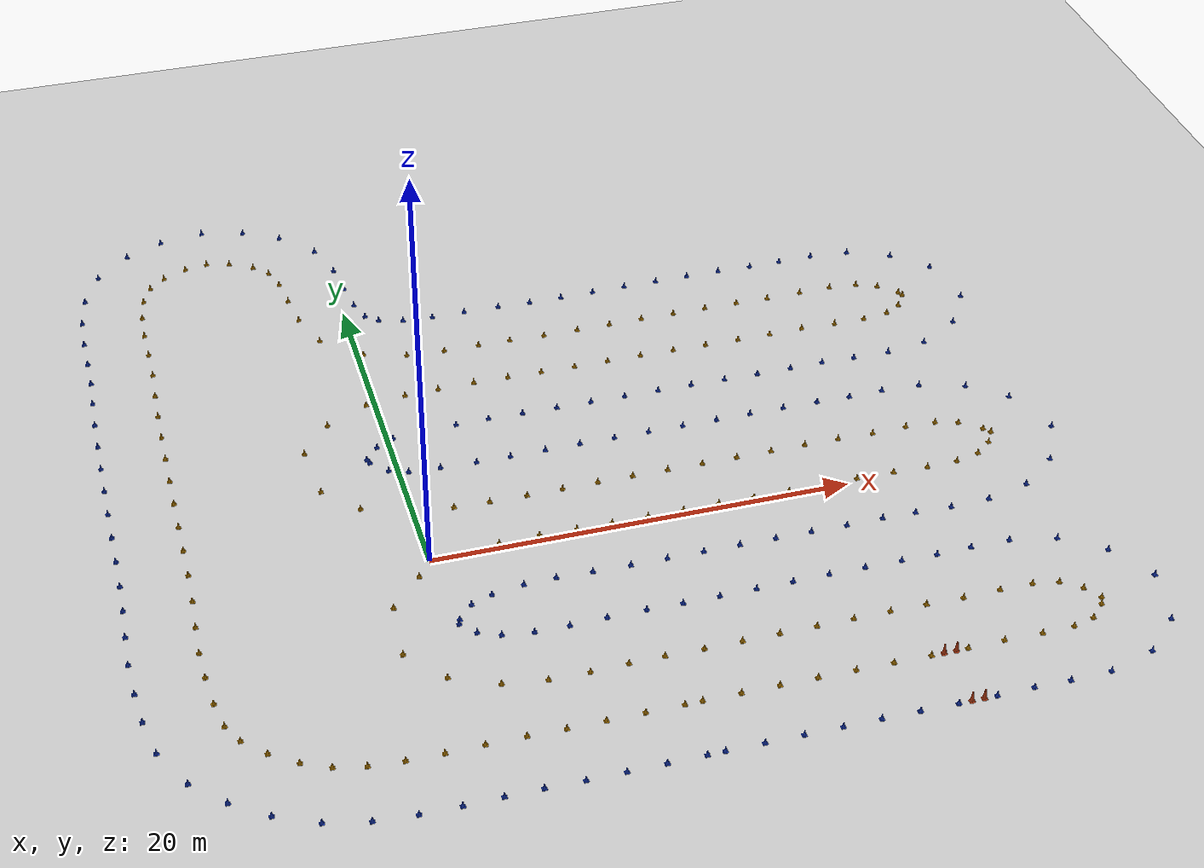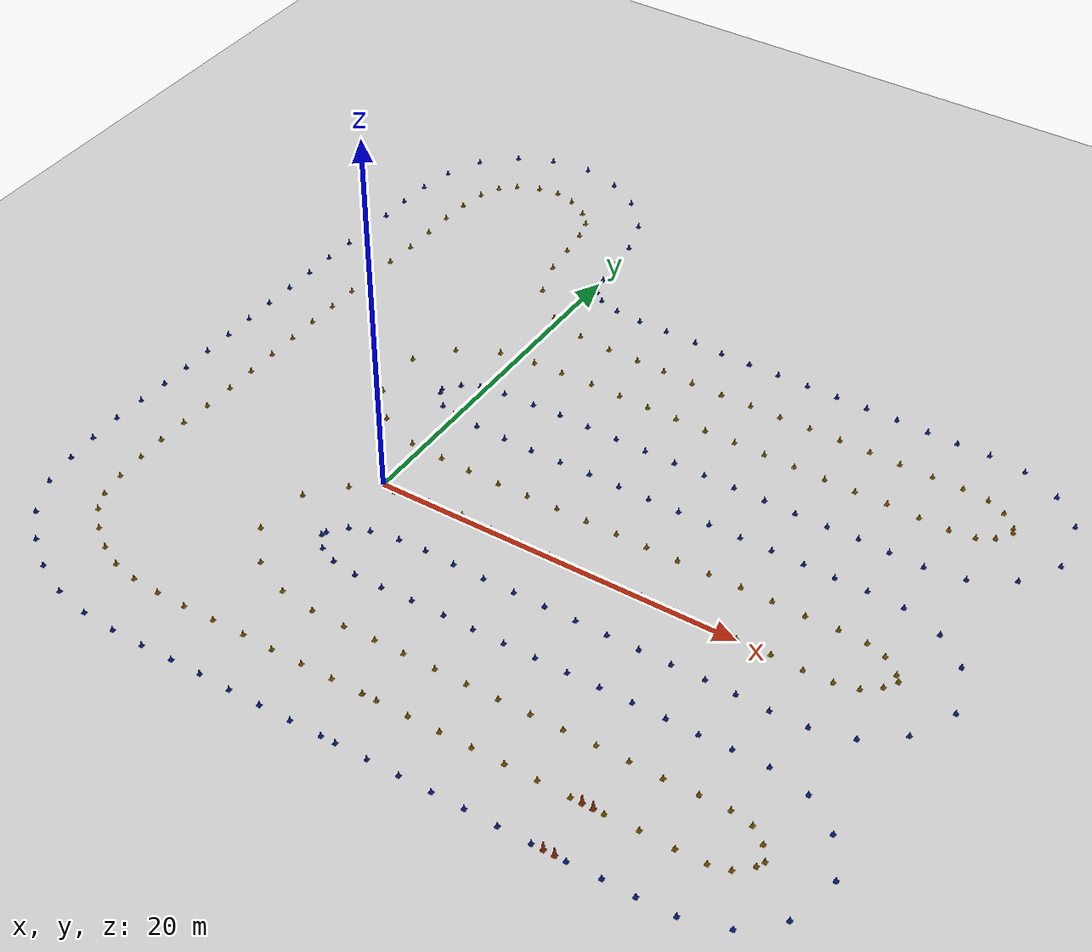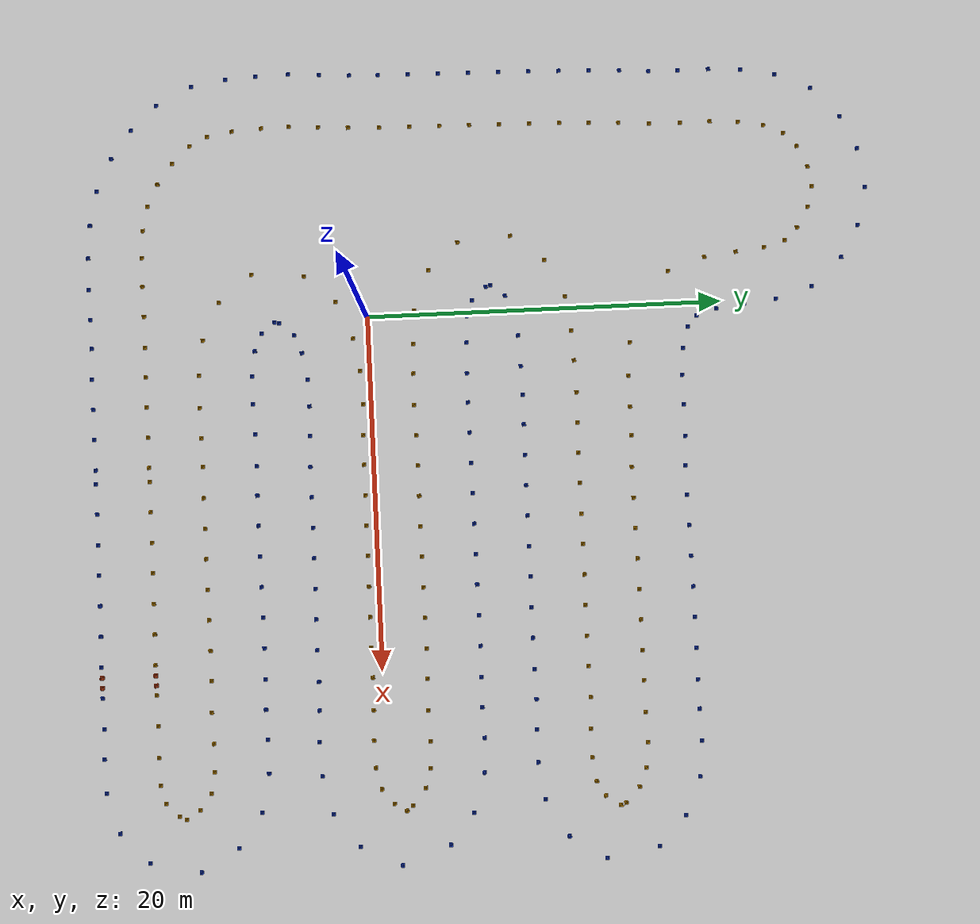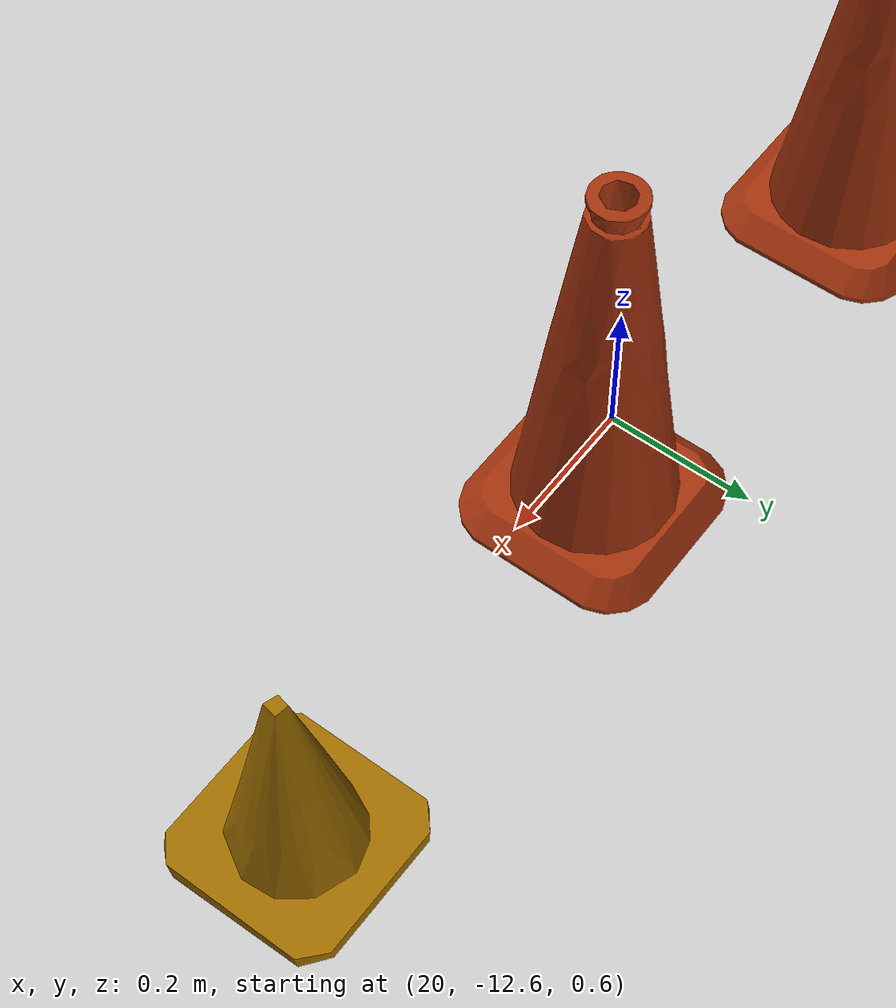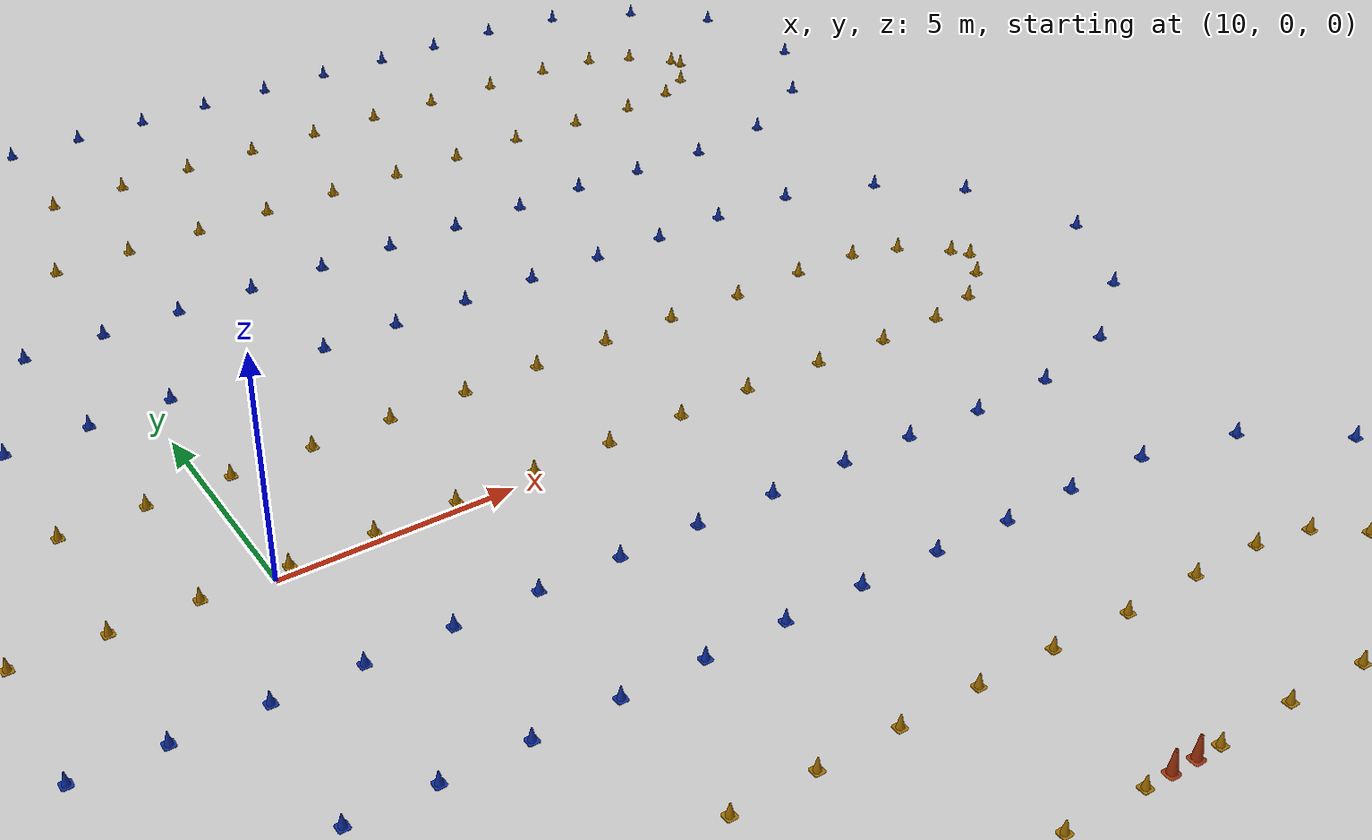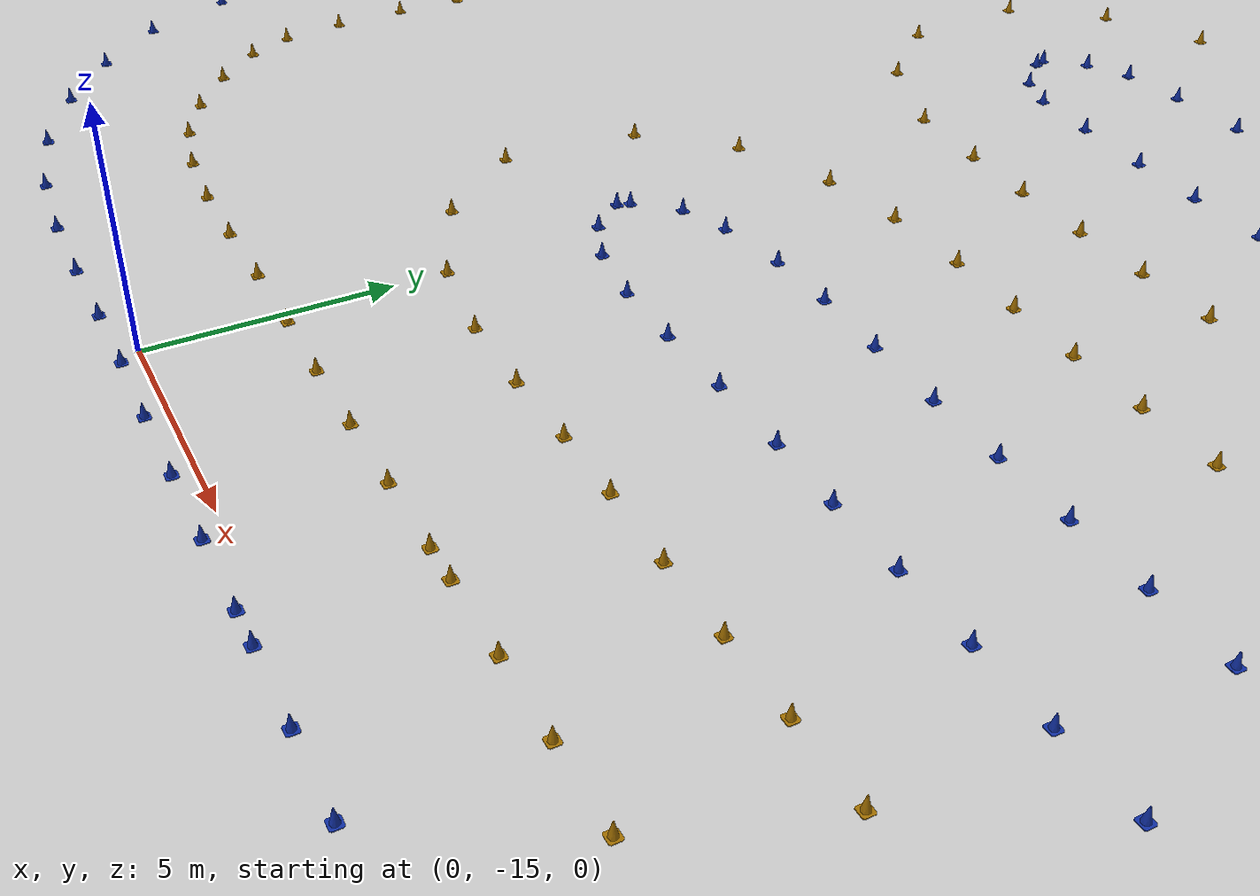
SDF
<sdf version='1.6'>
  <world name='comp_2021'>
    <gui fullscreen='0'>
      <camera name='user_camera'>
        <pose frame=''>-40 40 20 0 0.667643 -1</pose>
        <view_controller>orbit</view_controller>
        <projection_type>perspective</projection_type>
      </camera>
    </gui>

    <!-- WORLD SETTINGS -->
    <scene>
      <ambient>1.0 1.0 1.0 1.0</ambient>
      <shadows>false</shadows>
    </scene>

    <spherical_coordinates>
      <heading_deg>180</heading_deg>

      <!-- Appleton Tower coordinates -->
      <latitude_deg>-27.69056</latitude_deg>
      <longitude_deg>152.65461</longitude_deg>
    </spherical_coordinates>

    <light name='sun' type='directional'>
      <cast_shadows>1</cast_shadows>
      <pose frame=''>0 0 10 0 -0 0</pose>
      <diffuse>0.8 0.8 0.8 1</diffuse>
      <specular>0.1 0.1 0.1 1</specular>
      <attenuation>
        <range>1000</range>
        <constant>0.9</constant>
        <linear>0.01</linear>
        <quadratic>0.001</quadratic>
      </attenuation>
      <direction>-0.5 0.5 -1</direction>
    </light>

    <!-- MODELS -->
    <include>
      <uri>model://ground_plane</uri>
      <pose>0.0 0.0 0.0 0 0 0</pose>
    </include>

    <include>
      <uri>model://comp_2021</uri>
      <pose>0 0 0.5 0 0 0</pose>
    </include>

  </world>
</sdf>

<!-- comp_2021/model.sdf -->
<sdf version='1.6'>
  <model name='track'>

    <include>
      <pose>8.79689 -15.5 0.15 0 0 0</pose>
      <uri>model://blue_cone</uri>
      <name>blue_cone_0</name>

      <covariance x="0.01" y="0.01" xy="0.0"/>

    </include>

    <include>
      <pose>10.49493 -15.50029 0.15 0 0 0</pose>
      <uri>model://blue_cone</uri>
      <name>blue_cone_1</name>

      <covariance x="0.01" y="0.01" xy="0.0"/>

    </include>

    <include>
      <pose>12.192969999999999 -15.50058 0.15 0 0 0</pose>
      <uri>model://blue_cone</uri>
      <name>blue_cone_2</name>

      <covariance x="0.01" y="0.01" xy="0.0"/>

    </include>

    <include>
      <pose>13.891010000000001 -15.50087 0.15 0 0 0</pose>
      <uri>model://blue_cone</uri>
      <name>blue_cone_3</name>

      <covariance x="0.01" y="0.01" xy="0.0"/>

    </include>

    <include>
      <pose>15.589039999999999 -15.501170000000002 0.15 0 0 0</pose>
      <uri>model://blue_cone</uri>
      <name>blue_cone_4</name>

      <covariance x="0.01" y="0.01" xy="0.0"/>

    </include>

    <include>
      <pose>17.288710000000002 -15.515089999999999 0.15 0 0 0</pose>
      <uri>model://blue_cone</uri>
      <name>blue_cone_5</name>

      <covariance x="0.01" y="0.01" xy="0.0"/>

    </include>

    <include>
      <pose>18.988870000000002 -15.53315 0.15 0 0 0</pose>
      <uri>model://blue_cone</uri>
      <name>blue_cone_6</name>

      <covariance x="0.01" y="0.01" xy="0.0"/>

    </include>

    <include>
      <pose>20.713179999999998 -15.53485 0.15 0 0 0</pose>
      <uri>model://blue_cone</uri>
      <name>blue_cone_7</name>

      <covariance x="0.01" y="0.01" xy="0.0"/>

    </include>

    <include>
      <pose>22.412370000000003 -15.49125 0.15 0 0 0</pose>
      <uri>model://blue_cone</uri>
      <name>blue_cone_8</name>

      <covariance x="0.01" y="0.01" xy="0.0"/>

    </include>

    <include>
      <pose>24.06126 -15.527479999999999 0.15 0 0 0</pose>
      <uri>model://blue_cone</uri>
      <name>blue_cone_9</name>

      <covariance x="0.01" y="0.01" xy="0.0"/>

    </include>

    <include>
      <pose>25.954710000000002 -15.47296 0.15 0 0 0</pose>
      <uri>model://blue_cone</uri>
      <name>blue_cone_10</name>

      <covariance x="0.01" y="0.01" xy="0.0"/>

    </include>

    <include>
      <pose>28.172340000000002 -14.805979999999998 0.15 0 0 0</pose>
      <uri>model://blue_cone</uri>
      <name>blue_cone_11</name>

      <covariance x="0.01" y="0.01" xy="0.0"/>

    </include>

    <include>
      <pose>29.87006 -13.18842 0.15 0 0 0</pose>
      <uri>model://blue_cone</uri>
      <name>blue_cone_12</name>

      <covariance x="0.01" y="0.01" xy="0.0"/>

    </include>

    <include>
      <pose>30.4947 -10.39108 0.15 0 0 0</pose>
      <uri>model://blue_cone</uri>
      <name>blue_cone_13</name>

      <covariance x="0.01" y="0.01" xy="0.0"/>

    </include>

    <include>
      <pose>29.25613 -8.276897 0.15 0 0 0</pose>
      <uri>model://blue_cone</uri>
      <name>blue_cone_14</name>

      <covariance x="0.01" y="0.01" xy="0.0"/>

    </include>

    <include>
      <pose>27.388479999999998 -6.933025 0.15 0 0 0</pose>
      <uri>model://blue_cone</uri>
      <name>blue_cone_15</name>

      <covariance x="0.01" y="0.01" xy="0.0"/>

    </include>

    <include>
      <pose>25.25427 -6.467773 0.15 0 0 0</pose>
      <uri>model://blue_cone</uri>
      <name>blue_cone_16</name>

      <covariance x="0.01" y="0.01" xy="0.0"/>

    </include>

    <include>
      <pose>23.40361 -6.455289 0.15 0 0 0</pose>
      <uri>model://blue_cone</uri>
      <name>blue_cone_17</name>

      <covariance x="0.01" y="0.01" xy="0.0"/>

    </include>

    <include>
      <pose>21.74766 -6.50684 0.15 0 0 0</pose>
      <uri>model://blue_cone</uri>
      <name>blue_cone_18</name>

      <covariance x="0.01" y="0.01" xy="0.0"/>

    </include>

    <include>
      <pose>20.07179 -6.468646 0.15 0 0 0</pose>
      <uri>model://blue_cone</uri>
      <name>blue_cone_19</name>

      <covariance x="0.01" y="0.01" xy="0.0"/>

    </include>

    <include>
      <pose>18.345670000000002 -6.459494 0.15 0 0 0</pose>
      <uri>model://blue_cone</uri>
      <name>blue_cone_20</name>

      <covariance x="0.01" y="0.01" xy="0.0"/>

    </include>

    <include>
      <pose>16.64525 -6.473904 0.15 0 0 0</pose>
      <uri>model://blue_cone</uri>
      <name>blue_cone_21</name>

      <covariance x="0.01" y="0.01" xy="0.0"/>

    </include>

    <include>
      <pose>14.945020000000001 -6.4884699999999995 0.15 0 0 0</pose>
      <uri>model://blue_cone</uri>
      <name>blue_cone_22</name>

      <covariance x="0.01" y="0.01" xy="0.0"/>

    </include>

    <include>
      <pose>13.24164 -6.501314 0.15 0 0 0</pose>
      <uri>model://blue_cone</uri>
      <name>blue_cone_23</name>

      <covariance x="0.01" y="0.01" xy="0.0"/>

    </include>

    <include>
      <pose>11.5386 -6.513823 0.15 0 0 0</pose>
      <uri>model://blue_cone</uri>
      <name>blue_cone_24</name>

      <covariance x="0.01" y="0.01" xy="0.0"/>

    </include>

    <include>
      <pose>9.850877 -6.526781 0.15 0 0 0</pose>
      <uri>model://blue_cone</uri>
      <name>blue_cone_25</name>

      <covariance x="0.01" y="0.01" xy="0.0"/>

    </include>

    <include>
      <pose>8.202765 -6.500373000000001 0.15 0 0 0</pose>
      <uri>model://blue_cone</uri>
      <name>blue_cone_26</name>

      <covariance x="0.01" y="0.01" xy="0.0"/>

    </include>

    <include>
      <pose>6.407849 -6.515731 0.15 0 0 0</pose>
      <uri>model://blue_cone</uri>
      <name>blue_cone_27</name>

      <covariance x="0.01" y="0.01" xy="0.0"/>

    </include>

    <include>
      <pose>4.71948 -6.57222 0.15 0 0 0</pose>
      <uri>model://blue_cone</uri>
      <name>blue_cone_28</name>

      <covariance x="0.01" y="0.01" xy="0.0"/>

    </include>

    <include>
      <pose>3.145468 -6.551782 0.15 0 0 0</pose>
      <uri>model://blue_cone</uri>
      <name>blue_cone_29</name>

      <covariance x="0.01" y="0.01" xy="0.0"/>

    </include>

    <include>
      <pose>1.746531 -6.351077 0.15 0 0 0</pose>
      <uri>model://blue_cone</uri>
      <name>blue_cone_30</name>

      <covariance x="0.01" y="0.01" xy="0.0"/>

    </include>

    <include>
      <pose>0.7652611999999999 -5.920299 0.15 0 0 0</pose>
      <uri>model://blue_cone</uri>
      <name>blue_cone_31</name>

      <covariance x="0.01" y="0.01" xy="0.0"/>

    </include>

    <include>
      <pose>0.15050410000000003 -5.185045 0.15 0 0 0</pose>
      <uri>model://blue_cone</uri>
      <name>blue_cone_32</name>

      <covariance x="0.01" y="0.01" xy="0.0"/>

    </include>

    <include>
      <pose>0.23446489999999998 -4.922377 0.15 0 0 0</pose>
      <uri>model://blue_cone</uri>
      <name>blue_cone_33</name>

      <covariance x="0.01" y="0.01" xy="0.0"/>

    </include>

    <include>
      <pose>0.9523565 -4.112127 0.15 0 0 0</pose>
      <uri>model://blue_cone</uri>
      <name>blue_cone_34</name>

      <covariance x="0.01" y="0.01" xy="0.0"/>

    </include>

    <include>
      <pose>1.9622529999999998 -3.726687 0.15 0 0 0</pose>
      <uri>model://blue_cone</uri>
      <name>blue_cone_35</name>

      <covariance x="0.01" y="0.01" xy="0.0"/>

    </include>

    <include>
      <pose>3.474592 -3.468724 0.15 0 0 0</pose>
      <uri>model://blue_cone</uri>
      <name>blue_cone_36</name>

      <covariance x="0.01" y="0.01" xy="0.0"/>

    </include>

    <include>
      <pose>4.971986 -3.408813 0.15 0 0 0</pose>
      <uri>model://blue_cone</uri>
      <name>blue_cone_37</name>

      <covariance x="0.01" y="0.01" xy="0.0"/>

    </include>

    <include>
      <pose>6.637001 -3.4630629999999996 0.15 0 0 0</pose>
      <uri>model://blue_cone</uri>
      <name>blue_cone_38</name>

      <covariance x="0.01" y="0.01" xy="0.0"/>

    </include>

    <include>
      <pose>8.378223 -3.4995510000000003 0.15 0 0 0</pose>
      <uri>model://blue_cone</uri>
      <name>blue_cone_39</name>

      <covariance x="0.01" y="0.01" xy="0.0"/>

    </include>

    <include>
      <pose>10.08106 -3.4996769999999997 0.15 0 0 0</pose>
      <uri>model://blue_cone</uri>
      <name>blue_cone_40</name>

      <covariance x="0.01" y="0.01" xy="0.0"/>

    </include>

    <include>
      <pose>11.78388 -3.499803 0.15 0 0 0</pose>
      <uri>model://blue_cone</uri>
      <name>blue_cone_41</name>

      <covariance x="0.01" y="0.01" xy="0.0"/>

    </include>

    <include>
      <pose>13.486720000000002 -3.4999279999999997 0.15 0 0 0</pose>
      <uri>model://blue_cone</uri>
      <name>blue_cone_42</name>

      <covariance x="0.01" y="0.01" xy="0.0"/>

    </include>

    <include>
      <pose>15.18764 -3.5055970000000003 0.15 0 0 0</pose>
      <uri>model://blue_cone</uri>
      <name>blue_cone_43</name>

      <covariance x="0.01" y="0.01" xy="0.0"/>

    </include>

    <include>
      <pose>16.88605 -3.5185760000000004 0.15 0 0 0</pose>
      <uri>model://blue_cone</uri>
      <name>blue_cone_44</name>

      <covariance x="0.01" y="0.01" xy="0.0"/>

    </include>

    <include>
      <pose>18.59188 -3.527626 0.15 0 0 0</pose>
      <uri>model://blue_cone</uri>
      <name>blue_cone_45</name>

      <covariance x="0.01" y="0.01" xy="0.0"/>

    </include>

    <include>
      <pose>20.33933 -3.500722 0.15 0 0 0</pose>
      <uri>model://blue_cone</uri>
      <name>blue_cone_46</name>

      <covariance x="0.01" y="0.01" xy="0.0"/>

    </include>

    <include>
      <pose>21.9308 -3.5303379999999995 0.15 0 0 0</pose>
      <uri>model://blue_cone</uri>
      <name>blue_cone_47</name>

      <covariance x="0.01" y="0.01" xy="0.0"/>

    </include>

    <include>
      <pose>23.65697 -3.5986059999999997 0.15 0 0 0</pose>
      <uri>model://blue_cone</uri>
      <name>blue_cone_48</name>

      <covariance x="0.01" y="0.01" xy="0.0"/>

    </include>

    <include>
      <pose>25.548939999999998 -3.5299690000000004 0.15 0 0 0</pose>
      <uri>model://blue_cone</uri>
      <name>blue_cone_49</name>

      <covariance x="0.01" y="0.01" xy="0.0"/>

    </include>

    <include>
      <pose>27.64678 -2.99064 0.15 0 0 0</pose>
      <uri>model://blue_cone</uri>
      <name>blue_cone_50</name>

      <covariance x="0.01" y="0.01" xy="0.0"/>

    </include>

    <include>
      <pose>29.48863 -1.582211 0.15 0 0 0</pose>
      <uri>model://blue_cone</uri>
      <name>blue_cone_51</name>

      <covariance x="0.01" y="0.01" xy="0.0"/>

    </include>

    <include>
      <pose>30.619909999999997 0.7157594 0.15 0 0 0</pose>
      <uri>model://blue_cone</uri>
      <name>blue_cone_52</name>

      <covariance x="0.01" y="0.01" xy="0.0"/>

    </include>

    <include>
      <pose>29.61567 3.4165550000000002 0.15 0 0 0</pose>
      <uri>model://blue_cone</uri>
      <name>blue_cone_53</name>

      <covariance x="0.01" y="0.01" xy="0.0"/>

    </include>

    <include>
      <pose>27.91333 4.774024 0.15 0 0 0</pose>
      <uri>model://blue_cone</uri>
      <name>blue_cone_54</name>

      <covariance x="0.01" y="0.01" xy="0.0"/>

    </include>

    <include>
      <pose>25.750989999999998 5.456471 0.15 0 0 0</pose>
      <uri>model://blue_cone</uri>
      <name>blue_cone_55</name>

      <covariance x="0.01" y="0.01" xy="0.0"/>

    </include>

    <include>
      <pose>23.84129 5.538531 0.15 0 0 0</pose>
      <uri>model://blue_cone</uri>
      <name>blue_cone_56</name>

      <covariance x="0.01" y="0.01" xy="0.0"/>

    </include>

    <include>
      <pose>22.145410000000002 5.494133000000001 0.15 0 0 0</pose>
      <uri>model://blue_cone</uri>
      <name>blue_cone_57</name>

      <covariance x="0.01" y="0.01" xy="0.0"/>

    </include>

    <include>
      <pose>20.4887 5.525844 0.15 0 0 0</pose>
      <uri>model://blue_cone</uri>
      <name>blue_cone_58</name>

      <covariance x="0.01" y="0.01" xy="0.0"/>

    </include>

    <include>
      <pose>18.75949 5.534084 0.15 0 0 0</pose>
      <uri>model://blue_cone</uri>
      <name>blue_cone_59</name>

      <covariance x="0.01" y="0.01" xy="0.0"/>

    </include>

    <include>
      <pose>17.05999 5.519393 0.15 0 0 0</pose>
      <uri>model://blue_cone</uri>
      <name>blue_cone_60</name>

      <covariance x="0.01" y="0.01" xy="0.0"/>

    </include>

    <include>
      <pose>15.3605 5.504703 0.15 0 0 0</pose>
      <uri>model://blue_cone</uri>
      <name>blue_cone_61</name>

      <covariance x="0.01" y="0.01" xy="0.0"/>

    </include>

    <include>
      <pose>13.66429 5.499892 0.15 0 0 0</pose>
      <uri>model://blue_cone</uri>
      <name>blue_cone_62</name>

      <covariance x="0.01" y="0.01" xy="0.0"/>

    </include>

    <include>
      <pose>11.96199 5.499691 0.15 0 0 0</pose>
      <uri>model://blue_cone</uri>
      <name>blue_cone_63</name>

      <covariance x="0.01" y="0.01" xy="0.0"/>

    </include>

    <include>
      <pose>10.25968 5.49949 0.15 0 0 0</pose>
      <uri>model://blue_cone</uri>
      <name>blue_cone_64</name>

      <covariance x="0.01" y="0.01" xy="0.0"/>

    </include>

    <include>
      <pose>8.557373 5.49929 0.15 0 0 0</pose>
      <uri>model://blue_cone</uri>
      <name>blue_cone_65</name>

      <covariance x="0.01" y="0.01" xy="0.0"/>

    </include>

    <include>
      <pose>6.853613 5.47529 0.15 0 0 0</pose>
      <uri>model://blue_cone</uri>
      <name>blue_cone_66</name>

      <covariance x="0.01" y="0.01" xy="0.0"/>

    </include>

    <include>
      <pose>5.15646 5.451069 0.15 0 0 0</pose>
      <uri>model://blue_cone</uri>
      <name>blue_cone_67</name>

      <covariance x="0.01" y="0.01" xy="0.0"/>

    </include>

    <include>
      <pose>3.5249629999999996 5.470642 0.15 0 0 0</pose>
      <uri>model://blue_cone</uri>
      <name>blue_cone_68</name>

      <covariance x="0.01" y="0.01" xy="0.0"/>

    </include>

    <include>
      <pose>1.797132 5.5320599999999995 0.15 0 0 0</pose>
      <uri>model://blue_cone</uri>
      <name>blue_cone_69</name>

      <covariance x="0.01" y="0.01" xy="0.0"/>

    </include>

    <include>
      <pose>0.2987953 5.620685 0.15 0 0 0</pose>
      <uri>model://blue_cone</uri>
      <name>blue_cone_70</name>

      <covariance x="0.01" y="0.01" xy="0.0"/>

    </include>

    <include>
      <pose>-0.5785224 5.9444989999999995 0.15 0 0 0</pose>
      <uri>model://blue_cone</uri>
      <name>blue_cone_71</name>

      <covariance x="0.01" y="0.01" xy="0.0"/>

    </include>

    <include>
      <pose>-1.308592 6.760839 0.15 0 0 0</pose>
      <uri>model://blue_cone</uri>
      <name>blue_cone_72</name>

      <covariance x="0.01" y="0.01" xy="0.0"/>

    </include>

    <include>
      <pose>-1.39762 7.0307 0.15 0 0 0</pose>
      <uri>model://blue_cone</uri>
      <name>blue_cone_73</name>

      <covariance x="0.01" y="0.01" xy="0.0"/>

    </include>

    <include>
      <pose>-0.744753 7.806924 0.15 0 0 0</pose>
      <uri>model://blue_cone</uri>
      <name>blue_cone_74</name>

      <covariance x="0.01" y="0.01" xy="0.0"/>

    </include>

    <include>
      <pose>0.1345779 8.275603 0.15 0 0 0</pose>
      <uri>model://blue_cone</uri>
      <name>blue_cone_75</name>

      <covariance x="0.01" y="0.01" xy="0.0"/>

    </include>

    <include>
      <pose>1.531696 8.437706 0.15 0 0 0</pose>
      <uri>model://blue_cone</uri>
      <name>blue_cone_76</name>

      <covariance x="0.01" y="0.01" xy="0.0"/>

    </include>

    <include>
      <pose>3.257644 8.510859 0.15 0 0 0</pose>
      <uri>model://blue_cone</uri>
      <name>blue_cone_77</name>

      <covariance x="0.01" y="0.01" xy="0.0"/>

    </include>

    <include>
      <pose>4.860303 8.553554 0.15 0 0 0</pose>
      <uri>model://blue_cone</uri>
      <name>blue_cone_78</name>

      <covariance x="0.01" y="0.01" xy="0.0"/>

    </include>

    <include>
      <pose>6.5434980000000005 8.530477000000001 0.15 0 0 0</pose>
      <uri>model://blue_cone</uri>
      <name>blue_cone_79</name>

      <covariance x="0.01" y="0.01" xy="0.0"/>

    </include>

    <include>
      <pose>8.247355 8.502235 0.15 0 0 0</pose>
      <uri>model://blue_cone</uri>
      <name>blue_cone_80</name>

      <covariance x="0.01" y="0.01" xy="0.0"/>

    </include>

    <include>
      <pose>9.95412 8.499846 0.15 0 0 0</pose>
      <uri>model://blue_cone</uri>
      <name>blue_cone_81</name>

      <covariance x="0.01" y="0.01" xy="0.0"/>

    </include>

    <include>
      <pose>11.653260000000001 8.499425 0.15 0 0 0</pose>
      <uri>model://blue_cone</uri>
      <name>blue_cone_82</name>

      <covariance x="0.01" y="0.01" xy="0.0"/>

    </include>

    <include>
      <pose>13.352379999999998 8.499003 0.15 0 0 0</pose>
      <uri>model://blue_cone</uri>
      <name>blue_cone_83</name>

      <covariance x="0.01" y="0.01" xy="0.0"/>

    </include>

    <include>
      <pose>15.05161 8.497525 0.15 0 0 0</pose>
      <uri>model://blue_cone</uri>
      <name>blue_cone_84</name>

      <covariance x="0.01" y="0.01" xy="0.0"/>

    </include>

    <include>
      <pose>16.75214 8.480833 0.15 0 0 0</pose>
      <uri>model://blue_cone</uri>
      <name>blue_cone_85</name>

      <covariance x="0.01" y="0.01" xy="0.0"/>

    </include>

    <include>
      <pose>18.45267 8.464141 0.15 0 0 0</pose>
      <uri>model://blue_cone</uri>
      <name>blue_cone_86</name>

      <covariance x="0.01" y="0.01" xy="0.0"/>

    </include>

    <include>
      <pose>20.18119 8.469039 0.15 0 0 0</pose>
      <uri>model://blue_cone</uri>
      <name>blue_cone_87</name>

      <covariance x="0.01" y="0.01" xy="0.0"/>

    </include>

    <include>
      <pose>21.85081 8.508317 0.15 0 0 0</pose>
      <uri>model://blue_cone</uri>
      <name>blue_cone_88</name>

      <covariance x="0.01" y="0.01" xy="0.0"/>

    </include>

    <include>
      <pose>23.505570000000002 8.452136 0.15 0 0 0</pose>
      <uri>model://blue_cone</uri>
      <name>blue_cone_89</name>

      <covariance x="0.01" y="0.01" xy="0.0"/>

    </include>

    <include>
      <pose>25.32181 8.438680999999999 0.15 0 0 0</pose>
      <uri>model://blue_cone</uri>
      <name>blue_cone_90</name>

      <covariance x="0.01" y="0.01" xy="0.0"/>

    </include>

    <include>
      <pose>27.36337 8.748217 0.15 0 0 0</pose>
      <uri>model://blue_cone</uri>
      <name>blue_cone_91</name>

      <covariance x="0.01" y="0.01" xy="0.0"/>

    </include>

    <include>
      <pose>29.4417 9.982633 0.15 0 0 0</pose>
      <uri>model://blue_cone</uri>
      <name>blue_cone_92</name>

      <covariance x="0.01" y="0.01" xy="0.0"/>

    </include>

    <include>
      <pose>30.7221 12.00279 0.15 0 0 0</pose>
      <uri>model://blue_cone</uri>
      <name>blue_cone_93</name>

      <covariance x="0.01" y="0.01" xy="0.0"/>

    </include>

    <include>
      <pose>30.20512 14.9233 0.15 0 0 0</pose>
      <uri>model://blue_cone</uri>
      <name>blue_cone_94</name>

      <covariance x="0.01" y="0.01" xy="0.0"/>

    </include>

    <include>
      <pose>28.5961 16.460910000000002 0.15 0 0 0</pose>
      <uri>model://blue_cone</uri>
      <name>blue_cone_95</name>

      <covariance x="0.01" y="0.01" xy="0.0"/>

    </include>

    <include>
      <pose>26.51158 17.351129999999998 0.15 0 0 0</pose>
      <uri>model://blue_cone</uri>
      <name>blue_cone_96</name>

      <covariance x="0.01" y="0.01" xy="0.0"/>

    </include>

    <include>
      <pose>24.53734 17.54747 0.15 0 0 0</pose>
      <uri>model://blue_cone</uri>
      <name>blue_cone_97</name>

      <covariance x="0.01" y="0.01" xy="0.0"/>

    </include>

    <include>
      <pose>22.77645 17.51729 0.15 0 0 0</pose>
      <uri>model://blue_cone</uri>
      <name>blue_cone_98</name>

      <covariance x="0.01" y="0.01" xy="0.0"/>

    </include>

    <include>
      <pose>21.15735 17.50321 0.15 0 0 0</pose>
      <uri>model://blue_cone</uri>
      <name>blue_cone_99</name>

      <covariance x="0.01" y="0.01" xy="0.0"/>

    </include>

    <include>
      <pose>19.42025 17.53239 0.15 0 0 0</pose>
      <uri>model://blue_cone</uri>
      <name>blue_cone_100</name>

      <covariance x="0.01" y="0.01" xy="0.0"/>

    </include>

    <include>
      <pose>17.7071 17.52685 0.15 0 0 0</pose>
      <uri>model://blue_cone</uri>
      <name>blue_cone_101</name>

      <covariance x="0.01" y="0.01" xy="0.0"/>

    </include>

    <include>
      <pose>16.00769 17.51238 0.15 0 0 0</pose>
      <uri>model://blue_cone</uri>
      <name>blue_cone_102</name>

      <covariance x="0.01" y="0.01" xy="0.0"/>

    </include>

    <include>
      <pose>14.304860000000001 17.49946 0.15 0 0 0</pose>
      <uri>model://blue_cone</uri>
      <name>blue_cone_103</name>

      <covariance x="0.01" y="0.01" xy="0.0"/>

    </include>

    <include>
      <pose>12.59832 17.476129999999998 0.15 0 0 0</pose>
      <uri>model://blue_cone</uri>
      <name>blue_cone_104</name>

      <covariance x="0.01" y="0.01" xy="0.0"/>

    </include>

    <include>
      <pose>10.89581 17.44691 0.15 0 0 0</pose>
      <uri>model://blue_cone</uri>
      <name>blue_cone_105</name>

      <covariance x="0.01" y="0.01" xy="0.0"/>

    </include>

    <include>
      <pose>9.235472 17.44289 0.15 0 0 0</pose>
      <uri>model://blue_cone</uri>
      <name>blue_cone_106</name>

      <covariance x="0.01" y="0.01" xy="0.0"/>

    </include>

    <include>
      <pose>7.589136 17.51162 0.15 0 0 0</pose>
      <uri>model://blue_cone</uri>
      <name>blue_cone_107</name>

      <covariance x="0.01" y="0.01" xy="0.0"/>

    </include>

    <include>
      <pose>5.809601 17.52532 0.15 0 0 0</pose>
      <uri>model://blue_cone</uri>
      <name>blue_cone_108</name>

      <covariance x="0.01" y="0.01" xy="0.0"/>

    </include>

    <include>
      <pose>4.15097 17.52303 0.15 0 0 0</pose>
      <uri>model://blue_cone</uri>
      <name>blue_cone_109</name>

      <covariance x="0.01" y="0.01" xy="0.0"/>

    </include>

    <include>
      <pose>2.651351 17.639470000000003 0.15 0 0 0</pose>
      <uri>model://blue_cone</uri>
      <name>blue_cone_110</name>

      <covariance x="0.01" y="0.01" xy="0.0"/>

    </include>

    <include>
      <pose>1.4618879999999999 17.9786 0.15 0 0 0</pose>
      <uri>model://blue_cone</uri>
      <name>blue_cone_111</name>

      <covariance x="0.01" y="0.01" xy="0.0"/>

    </include>

    <include>
      <pose>0.8711742 18.49831 0.15 0 0 0</pose>
      <uri>model://blue_cone</uri>
      <name>blue_cone_112</name>

      <covariance x="0.01" y="0.01" xy="0.0"/>

    </include>

    <include>
      <pose>0.5196092000000001 19.63735 0.15 0 0 0</pose>
      <uri>model://blue_cone</uri>
      <name>blue_cone_113</name>

      <covariance x="0.01" y="0.01" xy="0.0"/>

    </include>

    <include>
      <pose>0.3270568 21.213910000000002 0.15 0 0 0</pose>
      <uri>model://blue_cone</uri>
      <name>blue_cone_114</name>

      <covariance x="0.01" y="0.01" xy="0.0"/>

    </include>

    <include>
      <pose>0.1140594 22.9959 0.15 0 0 0</pose>
      <uri>model://blue_cone</uri>
      <name>blue_cone_115</name>

      <covariance x="0.01" y="0.01" xy="0.0"/>

    </include>

    <include>
      <pose>-0.5154185 25.05451 0.15 0 0 0</pose>
      <uri>model://blue_cone</uri>
      <name>blue_cone_116</name>

      <covariance x="0.01" y="0.01" xy="0.0"/>

    </include>

    <include>
      <pose>-2.075313 26.82025 0.15 0 0 0</pose>
      <uri>model://blue_cone</uri>
      <name>blue_cone_117</name>

      <covariance x="0.01" y="0.01" xy="0.0"/>

    </include>

    <include>
      <pose>-3.867439 27.846729999999997 0.15 0 0 0</pose>
      <uri>model://blue_cone</uri>
      <name>blue_cone_118</name>

      <covariance x="0.01" y="0.01" xy="0.0"/>

    </include>

    <include>
      <pose>-6.00108 28.37929 0.15 0 0 0</pose>
      <uri>model://blue_cone</uri>
      <name>blue_cone_119</name>

      <covariance x="0.01" y="0.01" xy="0.0"/>

    </include>

    <include>
      <pose>-8.21226 28.06349 0.15 0 0 0</pose>
      <uri>model://blue_cone</uri>
      <name>blue_cone_120</name>

      <covariance x="0.01" y="0.01" xy="0.0"/>

    </include>

    <include>
      <pose>-10.09993 27.19528 0.15 0 0 0</pose>
      <uri>model://blue_cone</uri>
      <name>blue_cone_121</name>

      <covariance x="0.01" y="0.01" xy="0.0"/>

    </include>

    <include>
      <pose>-11.78507 25.62565 0.15 0 0 0</pose>
      <uri>model://blue_cone</uri>
      <name>blue_cone_122</name>

      <covariance x="0.01" y="0.01" xy="0.0"/>

    </include>

    <include>
      <pose>-12.6777 23.64299 0.15 0 0 0</pose>
      <uri>model://blue_cone</uri>
      <name>blue_cone_123</name>

      <covariance x="0.01" y="0.01" xy="0.0"/>

    </include>

    <include>
      <pose>-13.03012 21.72491 0.15 0 0 0</pose>
      <uri>model://blue_cone</uri>
      <name>blue_cone_124</name>

      <covariance x="0.01" y="0.01" xy="0.0"/>

    </include>

    <include>
      <pose>-13.1392 19.90714 0.15 0 0 0</pose>
      <uri>model://blue_cone</uri>
      <name>blue_cone_125</name>

      <covariance x="0.01" y="0.01" xy="0.0"/>

    </include>

    <include>
      <pose>-13.154739999999999 18.18133 0.15 0 0 0</pose>
      <uri>model://blue_cone</uri>
      <name>blue_cone_126</name>

      <covariance x="0.01" y="0.01" xy="0.0"/>

    </include>

    <include>
      <pose>-13.177010000000001 16.52994 0.15 0 0 0</pose>
      <uri>model://blue_cone</uri>
      <name>blue_cone_127</name>

      <covariance x="0.01" y="0.01" xy="0.0"/>

    </include>

    <include>
      <pose>-13.292760000000001 14.873439999999999 0.15 0 0 0</pose>
      <uri>model://blue_cone</uri>
      <name>blue_cone_128</name>

      <covariance x="0.01" y="0.01" xy="0.0"/>

    </include>

    <include>
      <pose>-13.38279 13.14025 0.15 0 0 0</pose>
      <uri>model://blue_cone</uri>
      <name>blue_cone_129</name>

      <covariance x="0.01" y="0.01" xy="0.0"/>

    </include>

    <include>
      <pose>-13.43798 11.42786 0.15 0 0 0</pose>
      <uri>model://blue_cone</uri>
      <name>blue_cone_130</name>

      <covariance x="0.01" y="0.01" xy="0.0"/>

    </include>

    <include>
      <pose>-13.48475 9.721461 0.15 0 0 0</pose>
      <uri>model://blue_cone</uri>
      <name>blue_cone_131</name>

      <covariance x="0.01" y="0.01" xy="0.0"/>

    </include>

    <include>
      <pose>-13.53152 8.015052 0.15 0 0 0</pose>
      <uri>model://blue_cone</uri>
      <name>blue_cone_132</name>

      <covariance x="0.01" y="0.01" xy="0.0"/>

    </include>

    <include>
      <pose>-13.565320000000002 6.31245 0.15 0 0 0</pose>
      <uri>model://blue_cone</uri>
      <name>blue_cone_133</name>

      <covariance x="0.01" y="0.01" xy="0.0"/>

    </include>

    <include>
      <pose>-13.59171 4.612038 0.15 0 0 0</pose>
      <uri>model://blue_cone</uri>
      <name>blue_cone_134</name>

      <covariance x="0.01" y="0.01" xy="0.0"/>

    </include>

    <include>
      <pose>-13.61811 2.91161 0.15 0 0 0</pose>
      <uri>model://blue_cone</uri>
      <name>blue_cone_135</name>

      <covariance x="0.01" y="0.01" xy="0.0"/>

    </include>

    <include>
      <pose>-13.64705 1.215924 0.15 0 0 0</pose>
      <uri>model://blue_cone</uri>
      <name>blue_cone_136</name>

      <covariance x="0.01" y="0.01" xy="0.0"/>

    </include>

    <include>
      <pose>-13.70985 -0.42630680000000004 0.15 0 0 0</pose>
      <uri>model://blue_cone</uri>
      <name>blue_cone_137</name>

      <covariance x="0.01" y="0.01" xy="0.0"/>

    </include>

    <include>
      <pose>-13.825879999999998 -2.118713 0.15 0 0 0</pose>
      <uri>model://blue_cone</uri>
      <name>blue_cone_138</name>

      <covariance x="0.01" y="0.01" xy="0.0"/>

    </include>

    <include>
      <pose>-13.918989999999999 -3.8688230000000003 0.15 0 0 0</pose>
      <uri>model://blue_cone</uri>
      <name>blue_cone_139</name>

      <covariance x="0.01" y="0.01" xy="0.0"/>

    </include>

    <include>
      <pose>-13.88756 -5.7059690000000005 0.15 0 0 0</pose>
      <uri>model://blue_cone</uri>
      <name>blue_cone_140</name>

      <covariance x="0.01" y="0.01" xy="0.0"/>

    </include>

    <include>
      <pose>-13.777679999999998 -7.442092999999999 0.15 0 0 0</pose>
      <uri>model://blue_cone</uri>
      <name>blue_cone_141</name>

      <covariance x="0.01" y="0.01" xy="0.0"/>

    </include>

    <include>
      <pose>-13.45904 -9.373876 0.15 0 0 0</pose>
      <uri>model://blue_cone</uri>
      <name>blue_cone_142</name>

      <covariance x="0.01" y="0.01" xy="0.0"/>

    </include>

    <include>
      <pose>-12.4734 -11.39717 0.15 0 0 0</pose>
      <uri>model://blue_cone</uri>
      <name>blue_cone_143</name>

      <covariance x="0.01" y="0.01" xy="0.0"/>

    </include>

    <include>
      <pose>-11.102730000000001 -12.86398 0.15 0 0 0</pose>
      <uri>model://blue_cone</uri>
      <name>blue_cone_144</name>

      <covariance x="0.01" y="0.01" xy="0.0"/>

    </include>

    <include>
      <pose>-9.543593 -14.02694 0.15 0 0 0</pose>
      <uri>model://blue_cone</uri>
      <name>blue_cone_145</name>

      <covariance x="0.01" y="0.01" xy="0.0"/>

    </include>

    <include>
      <pose>-7.7101630000000005 -14.917179999999998 0.15 0 0 0</pose>
      <uri>model://blue_cone</uri>
      <name>blue_cone_146</name>

      <covariance x="0.01" y="0.01" xy="0.0"/>

    </include>

    <include>
      <pose>-5.778424 -15.36134 0.15 0 0 0</pose>
      <uri>model://blue_cone</uri>
      <name>blue_cone_147</name>

      <covariance x="0.01" y="0.01" xy="0.0"/>

    </include>

    <include>
      <pose>-3.9336279999999997 -15.51622 0.15 0 0 0</pose>
      <uri>model://blue_cone</uri>
      <name>blue_cone_148</name>

      <covariance x="0.01" y="0.01" xy="0.0"/>

    </include>

    <include>
      <pose>-2.160993 -15.5335 0.15 0 0 0</pose>
      <uri>model://blue_cone</uri>
      <name>blue_cone_149</name>

      <covariance x="0.01" y="0.01" xy="0.0"/>

    </include>

    <include>
      <pose>-0.45830290000000007 -15.50195 0.15 0 0 0</pose>
      <uri>model://blue_cone</uri>
      <name>blue_cone_150</name>

      <covariance x="0.01" y="0.01" xy="0.0"/>

    </include>

    <include>
      <pose>1.1901190000000001 -15.492920000000002 0.15 0 0 0</pose>
      <uri>model://blue_cone</uri>
      <name>blue_cone_151</name>

      <covariance x="0.01" y="0.01" xy="0.0"/>

    </include>

    <include>
      <pose>2.907752 -15.528070000000001 0.15 0 0 0</pose>
      <uri>model://blue_cone</uri>
      <name>blue_cone_152</name>

      <covariance x="0.01" y="0.01" xy="0.0"/>

    </include>

    <include>
      <pose>4.618753 -15.525479999999998 0.15 0 0 0</pose>
      <uri>model://blue_cone</uri>
      <name>blue_cone_153</name>

      <covariance x="0.01" y="0.01" xy="0.0"/>

    </include>

    <include>
      <pose>6.320954 -15.514829999999998 0.15 0 0 0</pose>
      <uri>model://blue_cone</uri>
      <name>blue_cone_154</name>

      <covariance x="0.01" y="0.01" xy="0.0"/>

    </include>

    <include>
      <pose>8.023155000000001 -15.504170000000002 0.15 0 0 0</pose>
      <uri>model://blue_cone</uri>
      <name>blue_cone_155</name>

      <covariance x="0.01" y="0.01" xy="0.0"/>

    </include>

    <include>
      <pose>8.79689 -12.5 0.15 0 0 0</pose>
      <uri>model://yellow_cone</uri>
      <name>yellow_cone_156</name>

      <covariance x="0.01" y="0.01" xy="0.0"/>

    </include>

    <include>
      <pose>10.49885 -12.5003 0.15 0 0 0</pose>
      <uri>model://yellow_cone</uri>
      <name>yellow_cone_157</name>

      <covariance x="0.01" y="0.01" xy="0.0"/>

    </include>

    <include>
      <pose>12.20081 -12.5006 0.15 0 0 0</pose>
      <uri>model://yellow_cone</uri>
      <name>yellow_cone_158</name>

      <covariance x="0.01" y="0.01" xy="0.0"/>

    </include>

    <include>
      <pose>13.90277 -12.500910000000001 0.15 0 0 0</pose>
      <uri>model://yellow_cone</uri>
      <name>yellow_cone_159</name>

      <covariance x="0.01" y="0.01" xy="0.0"/>

    </include>

    <include>
      <pose>15.60474 -12.50121 0.15 0 0 0</pose>
      <uri>model://yellow_cone</uri>
      <name>yellow_cone_160</name>

      <covariance x="0.01" y="0.01" xy="0.0"/>

    </include>

    <include>
      <pose>17.304920000000003 -12.515130000000001 0.15 0 0 0</pose>
      <uri>model://yellow_cone</uri>
      <name>yellow_cone_161</name>

      <covariance x="0.01" y="0.01" xy="0.0"/>

    </include>

    <include>
      <pose>19.00457 -12.53319 0.15 0 0 0</pose>
      <uri>model://yellow_cone</uri>
      <name>yellow_cone_162</name>

      <covariance x="0.01" y="0.01" xy="0.0"/>

    </include>

    <include>
      <pose>20.68018 -12.535060000000001 0.15 0 0 0</pose>
      <uri>model://yellow_cone</uri>
      <name>yellow_cone_163</name>

      <covariance x="0.01" y="0.01" xy="0.0"/>

    </include>

    <include>
      <pose>22.37969 -12.49146 0.15 0 0 0</pose>
      <uri>model://yellow_cone</uri>
      <name>yellow_cone_164</name>

      <covariance x="0.01" y="0.01" xy="0.0"/>

    </include>

    <include>
      <pose>24.12981 -12.52828 0.15 0 0 0</pose>
      <uri>model://yellow_cone</uri>
      <name>yellow_cone_165</name>

      <covariance x="0.01" y="0.01" xy="0.0"/>

    </include>

    <include>
      <pose>25.63267 -12.490310000000001 0.15 0 0 0</pose>
      <uri>model://yellow_cone</uri>
      <name>yellow_cone_166</name>

      <covariance x="0.01" y="0.01" xy="0.0"/>

    </include>

    <include>
      <pose>26.65656 -12.21798 0.15 0 0 0</pose>
      <uri>model://yellow_cone</uri>
      <name>yellow_cone_167</name>

      <covariance x="0.01" y="0.01" xy="0.0"/>

    </include>

    <include>
      <pose>27.392329999999998 -11.49727 0.15 0 0 0</pose>
      <uri>model://yellow_cone</uri>
      <name>yellow_cone_168</name>

      <covariance x="0.01" y="0.01" xy="0.0"/>

    </include>

    <include>
      <pose>27.582359999999998 -11.10453 0.15 0 0 0</pose>
      <uri>model://yellow_cone</uri>
      <name>yellow_cone_169</name>

      <covariance x="0.01" y="0.01" xy="0.0"/>

    </include>

    <include>
      <pose>27.078940000000003 -10.34074 0.15 0 0 0</pose>
      <uri>model://yellow_cone</uri>
      <name>yellow_cone_170</name>

      <covariance x="0.01" y="0.01" xy="0.0"/>

    </include>

    <include>
      <pose>26.218059999999998 -9.694744 0.15 0 0 0</pose>
      <uri>model://yellow_cone</uri>
      <name>yellow_cone_171</name>

      <covariance x="0.01" y="0.01" xy="0.0"/>

    </include>

    <include>
      <pose>25.04074 -9.460099000000001 0.15 0 0 0</pose>
      <uri>model://yellow_cone</uri>
      <name>yellow_cone_172</name>

      <covariance x="0.01" y="0.01" xy="0.0"/>

    </include>

    <include>
      <pose>23.49314 -9.453952000000001 0.15 0 0 0</pose>
      <uri>model://yellow_cone</uri>
      <name>yellow_cone_173</name>

      <covariance x="0.01" y="0.01" xy="0.0"/>

    </include>

    <include>
      <pose>21.750870000000003 -9.506809 0.15 0 0 0</pose>
      <uri>model://yellow_cone</uri>
      <name>yellow_cone_174</name>

      <covariance x="0.01" y="0.01" xy="0.0"/>

    </include>

    <include>
      <pose>20.02775 -9.468283 0.15 0 0 0</pose>
      <uri>model://yellow_cone</uri>
      <name>yellow_cone_175</name>

      <covariance x="0.01" y="0.01" xy="0.0"/>

    </include>

    <include>
      <pose>18.35396 -9.459479 0.15 0 0 0</pose>
      <uri>model://yellow_cone</uri>
      <name>yellow_cone_176</name>

      <covariance x="0.01" y="0.01" xy="0.0"/>

    </include>

    <include>
      <pose>16.6545 -9.473889 0.15 0 0 0</pose>
      <uri>model://yellow_cone</uri>
      <name>yellow_cone_177</name>

      <covariance x="0.01" y="0.01" xy="0.0"/>

    </include>

    <include>
      <pose>14.95485 -9.488453999999999 0.15 0 0 0</pose>
      <uri>model://yellow_cone</uri>
      <name>yellow_cone_178</name>

      <covariance x="0.01" y="0.01" xy="0.0"/>

    </include>

    <include>
      <pose>13.258339999999999 -9.501255 0.15 0 0 0</pose>
      <uri>model://yellow_cone</uri>
      <name>yellow_cone_179</name>

      <covariance x="0.01" y="0.01" xy="0.0"/>

    </include>

    <include>
      <pose>11.56149 -9.513727000000001 0.15 0 0 0</pose>
      <uri>model://yellow_cone</uri>
      <name>yellow_cone_180</name>

      <covariance x="0.01" y="0.01" xy="0.0"/>

    </include>

    <include>
      <pose>9.849332 -9.526745 0.15 0 0 0</pose>
      <uri>model://yellow_cone</uri>
      <name>yellow_cone_181</name>

      <covariance x="0.01" y="0.01" xy="0.0"/>

    </include>

    <include>
      <pose>8.098127 -9.498547 0.15 0 0 0</pose>
      <uri>model://yellow_cone</uri>
      <name>yellow_cone_182</name>

      <covariance x="0.01" y="0.01" xy="0.0"/>

    </include>

    <include>
      <pose>6.49403 -9.514491 0.15 0 0 0</pose>
      <uri>model://yellow_cone</uri>
      <name>yellow_cone_183</name>

      <covariance x="0.01" y="0.01" xy="0.0"/>

    </include>

    <include>
      <pose>4.784315 -9.571507 0.15 0 0 0</pose>
      <uri>model://yellow_cone</uri>
      <name>yellow_cone_184</name>

      <covariance x="0.01" y="0.01" xy="0.0"/>

    </include>

    <include>
      <pose>2.959647 -9.545983 0.15 0 0 0</pose>
      <uri>model://yellow_cone</uri>
      <name>yellow_cone_185</name>

      <covariance x="0.01" y="0.01" xy="0.0"/>

    </include>

    <include>
      <pose>0.9992856 -9.256391 0.15 0 0 0</pose>
      <uri>model://yellow_cone</uri>
      <name>yellow_cone_186</name>

      <covariance x="0.01" y="0.01" xy="0.0"/>

    </include>

    <include>
      <pose>-1.087284 -8.279549000000001 0.15 0 0 0</pose>
      <uri>model://yellow_cone</uri>
      <name>yellow_cone_187</name>

      <covariance x="0.01" y="0.01" xy="0.0"/>

    </include>

    <include>
      <pose>-2.592546 -6.39682 0.15 0 0 0</pose>
      <uri>model://yellow_cone</uri>
      <name>yellow_cone_188</name>

      <covariance x="0.01" y="0.01" xy="0.0"/>

    </include>

    <include>
      <pose>-2.3639259999999997 -3.424207 0.15 0 0 0</pose>
      <uri>model://yellow_cone</uri>
      <name>yellow_cone_189</name>

      <covariance x="0.01" y="0.01" xy="0.0"/>

    </include>

    <include>
      <pose>-0.8389496 -1.7070900000000002 0.15 0 0 0</pose>
      <uri>model://yellow_cone</uri>
      <name>yellow_cone_190</name>

      <covariance x="0.01" y="0.01" xy="0.0"/>

    </include>

    <include>
      <pose>1.27315 -0.8069972 0.15 0 0 0</pose>
      <uri>model://yellow_cone</uri>
      <name>yellow_cone_191</name>

      <covariance x="0.01" y="0.01" xy="0.0"/>

    </include>

    <include>
      <pose>3.11064 -0.49096320000000004 0.15 0 0 0</pose>
      <uri>model://yellow_cone</uri>
      <name>yellow_cone_192</name>

      <covariance x="0.01" y="0.01" xy="0.0"/>

    </include>

    <include>
      <pose>5.007768 -0.4090528 0.15 0 0 0</pose>
      <uri>model://yellow_cone</uri>
      <name>yellow_cone_193</name>

      <covariance x="0.01" y="0.01" xy="0.0"/>

    </include>

    <include>
      <pose>6.740854 -0.46486279999999996 0.15 0 0 0</pose>
      <uri>model://yellow_cone</uri>
      <name>yellow_cone_194</name>

      <covariance x="0.01" y="0.01" xy="0.0"/>

    </include>

    <include>
      <pose>8.398441 -0.49962460000000003 0.15 0 0 0</pose>
      <uri>model://yellow_cone</uri>
      <name>yellow_cone_195</name>

      <covariance x="0.01" y="0.01" xy="0.0"/>

    </include>

    <include>
      <pose>10.09561 -0.4997299 0.15 0 0 0</pose>
      <uri>model://yellow_cone</uri>
      <name>yellow_cone_196</name>

      <covariance x="0.01" y="0.01" xy="0.0"/>

    </include>

    <include>
      <pose>11.792769999999999 -0.49983500000000003 0.15 0 0 0</pose>
      <uri>model://yellow_cone</uri>
      <name>yellow_cone_197</name>

      <covariance x="0.01" y="0.01" xy="0.0"/>

    </include>

    <include>
      <pose>13.489939999999999 -0.4999403 0.15 0 0 0</pose>
      <uri>model://yellow_cone</uri>
      <name>yellow_cone_198</name>

      <covariance x="0.01" y="0.01" xy="0.0"/>

    </include>

    <include>
      <pose>15.18896 -0.5055988 0.15 0 0 0</pose>
      <uri>model://yellow_cone</uri>
      <name>yellow_cone_199</name>

      <covariance x="0.01" y="0.01" xy="0.0"/>

    </include>

    <include>
      <pose>16.89045 -0.5185807 0.15 0 0 0</pose>
      <uri>model://yellow_cone</uri>
      <name>yellow_cone_200</name>

      <covariance x="0.01" y="0.01" xy="0.0"/>

    </include>

    <include>
      <pose>18.584529999999997 -0.5276694000000001 0.15 0 0 0</pose>
      <uri>model://yellow_cone</uri>
      <name>yellow_cone_201</name>

      <covariance x="0.01" y="0.01" xy="0.0"/>

    </include>

    <include>
      <pose>20.2365 -0.5024877000000001 0.15 0 0 0</pose>
      <uri>model://yellow_cone</uri>
      <name>yellow_cone_202</name>

      <covariance x="0.01" y="0.01" xy="0.0"/>

    </include>

    <include>
      <pose>22.04334 -0.5324563 0.15 0 0 0</pose>
      <uri>model://yellow_cone</uri>
      <name>yellow_cone_203</name>

      <covariance x="0.01" y="0.01" xy="0.0"/>

    </include>

    <include>
      <pose>23.71435 -0.5991854999999999 0.15 0 0 0</pose>
      <uri>model://yellow_cone</uri>
      <name>yellow_cone_204</name>

      <covariance x="0.01" y="0.01" xy="0.0"/>

    </include>

    <include>
      <pose>25.2179 -0.548383 0.15 0 0 0</pose>
      <uri>model://yellow_cone</uri>
      <name>yellow_cone_205</name>

      <covariance x="0.01" y="0.01" xy="0.0"/>

    </include>

    <include>
      <pose>26.40332 -0.260592 0.15 0 0 0</pose>
      <uri>model://yellow_cone</uri>
      <name>yellow_cone_206</name>

      <covariance x="0.01" y="0.01" xy="0.0"/>

    </include>

    <include>
      <pose>27.23191 0.394243 0.15 0 0 0</pose>
      <uri>model://yellow_cone</uri>
      <name>yellow_cone_207</name>

      <covariance x="0.01" y="0.01" xy="0.0"/>

    </include>

    <include>
      <pose>27.64351 1.072329 0.15 0 0 0</pose>
      <uri>model://yellow_cone</uri>
      <name>yellow_cone_208</name>

      <covariance x="0.01" y="0.01" xy="0.0"/>

    </include>

    <include>
      <pose>27.382509999999996 1.413749 0.15 0 0 0</pose>
      <uri>model://yellow_cone</uri>
      <name>yellow_cone_209</name>

      <covariance x="0.01" y="0.01" xy="0.0"/>

    </include>

    <include>
      <pose>26.43465 2.16381 0.15 0 0 0</pose>
      <uri>model://yellow_cone</uri>
      <name>yellow_cone_210</name>

      <covariance x="0.01" y="0.01" xy="0.0"/>

    </include>

    <include>
      <pose>25.37175 2.480673 0.15 0 0 0</pose>
      <uri>model://yellow_cone</uri>
      <name>yellow_cone_211</name>

      <covariance x="0.01" y="0.01" xy="0.0"/>

    </include>

    <include>
      <pose>23.88726 2.538902 0.15 0 0 0</pose>
      <uri>model://yellow_cone</uri>
      <name>yellow_cone_212</name>

      <covariance x="0.01" y="0.01" xy="0.0"/>

    </include>

    <include>
      <pose>22.18435 2.494398 0.15 0 0 0</pose>
      <uri>model://yellow_cone</uri>
      <name>yellow_cone_213</name>

      <covariance x="0.01" y="0.01" xy="0.0"/>

    </include>

    <include>
      <pose>20.44197 2.526242 0.15 0 0 0</pose>
      <uri>model://yellow_cone</uri>
      <name>yellow_cone_214</name>

      <covariance x="0.01" y="0.01" xy="0.0"/>

    </include>

    <include>
      <pose>18.771279999999997 2.534107 0.15 0 0 0</pose>
      <uri>model://yellow_cone</uri>
      <name>yellow_cone_215</name>

      <covariance x="0.01" y="0.01" xy="0.0"/>

    </include>

    <include>
      <pose>17.07091 2.519413 0.15 0 0 0</pose>
      <uri>model://yellow_cone</uri>
      <name>yellow_cone_216</name>

      <covariance x="0.01" y="0.01" xy="0.0"/>

    </include>

    <include>
      <pose>15.37054 2.5047200000000003 0.15 0 0 0</pose>
      <uri>model://yellow_cone</uri>
      <name>yellow_cone_217</name>

      <covariance x="0.01" y="0.01" xy="0.0"/>

    </include>

    <include>
      <pose>13.666770000000001 2.499899 0.15 0 0 0</pose>
      <uri>model://yellow_cone</uri>
      <name>yellow_cone_218</name>

      <covariance x="0.01" y="0.01" xy="0.0"/>

    </include>

    <include>
      <pose>11.96909 2.499711 0.15 0 0 0</pose>
      <uri>model://yellow_cone</uri>
      <name>yellow_cone_219</name>

      <covariance x="0.01" y="0.01" xy="0.0"/>

    </include>

    <include>
      <pose>10.271410000000001 2.499523 0.15 0 0 0</pose>
      <uri>model://yellow_cone</uri>
      <name>yellow_cone_220</name>

      <covariance x="0.01" y="0.01" xy="0.0"/>

    </include>

    <include>
      <pose>8.573725 2.499335 0.15 0 0 0</pose>
      <uri>model://yellow_cone</uri>
      <name>yellow_cone_221</name>

      <covariance x="0.01" y="0.01" xy="0.0"/>

    </include>

    <include>
      <pose>6.877858 2.475397 0.15 0 0 0</pose>
      <uri>model://yellow_cone</uri>
      <name>yellow_cone_222</name>

      <covariance x="0.01" y="0.01" xy="0.0"/>

    </include>

    <include>
      <pose>5.175394 2.451157 0.15 0 0 0</pose>
      <uri>model://yellow_cone</uri>
      <name>yellow_cone_223</name>

      <covariance x="0.01" y="0.01" xy="0.0"/>

    </include>

    <include>
      <pose>3.407457 2.472963 0.15 0 0 0</pose>
      <uri>model://yellow_cone</uri>
      <name>yellow_cone_224</name>

      <covariance x="0.01" y="0.01" xy="0.0"/>

    </include>

    <include>
      <pose>1.737962 2.5326470000000003 0.15 0 0 0</pose>
      <uri>model://yellow_cone</uri>
      <name>yellow_cone_225</name>

      <covariance x="0.01" y="0.01" xy="0.0"/>

    </include>

    <include>
      <pose>-0.15436529999999998 2.655234 0.15 0 0 0</pose>
      <uri>model://yellow_cone</uri>
      <name>yellow_cone_226</name>

      <covariance x="0.01" y="0.01" xy="0.0"/>

    </include>

    <include>
      <pose>-2.4020580000000002 3.56279 0.15 0 0 0</pose>
      <uri>model://yellow_cone</uri>
      <name>yellow_cone_227</name>

      <covariance x="0.01" y="0.01" xy="0.0"/>

    </include>

    <include>
      <pose>-3.913738 5.274508 0.15 0 0 0</pose>
      <uri>model://yellow_cone</uri>
      <name>yellow_cone_228</name>

      <covariance x="0.01" y="0.01" xy="0.0"/>

    </include>

    <include>
      <pose>-4.140427 8.244469 0.15 0 0 0</pose>
      <uri>model://yellow_cone</uri>
      <name>yellow_cone_229</name>

      <covariance x="0.01" y="0.01" xy="0.0"/>

    </include>

    <include>
      <pose>-2.681155 10.09793 0.15 0 0 0</pose>
      <uri>model://yellow_cone</uri>
      <name>yellow_cone_230</name>

      <covariance x="0.01" y="0.01" xy="0.0"/>

    </include>

    <include>
      <pose>-0.5793665 11.18939 0.15 0 0 0</pose>
      <uri>model://yellow_cone</uri>
      <name>yellow_cone_231</name>

      <covariance x="0.01" y="0.01" xy="0.0"/>

    </include>

    <include>
      <pose>1.393709 11.434510000000001 0.15 0 0 0</pose>
      <uri>model://yellow_cone</uri>
      <name>yellow_cone_232</name>

      <covariance x="0.01" y="0.01" xy="0.0"/>

    </include>

    <include>
      <pose>3.064492 11.50463 0.15 0 0 0</pose>
      <uri>model://yellow_cone</uri>
      <name>yellow_cone_233</name>

      <covariance x="0.01" y="0.01" xy="0.0"/>

    </include>

    <include>
      <pose>4.860062999999999 11.55355 0.15 0 0 0</pose>
      <uri>model://yellow_cone</uri>
      <name>yellow_cone_234</name>

      <covariance x="0.01" y="0.01" xy="0.0"/>

    </include>

    <include>
      <pose>6.576489 11.530289999999999 0.15 0 0 0</pose>
      <uri>model://yellow_cone</uri>
      <name>yellow_cone_235</name>

      <covariance x="0.01" y="0.01" xy="0.0"/>

    </include>

    <include>
      <pose>8.272155 11.5021 0.15 0 0 0</pose>
      <uri>model://yellow_cone</uri>
      <name>yellow_cone_236</name>

      <covariance x="0.01" y="0.01" xy="0.0"/>

    </include>

    <include>
      <pose>9.965369 11.49982 0.15 0 0 0</pose>
      <uri>model://yellow_cone</uri>
      <name>yellow_cone_237</name>

      <covariance x="0.01" y="0.01" xy="0.0"/>

    </include>

    <include>
      <pose>11.66623 11.49939 0.15 0 0 0</pose>
      <uri>model://yellow_cone</uri>
      <name>yellow_cone_238</name>

      <covariance x="0.01" y="0.01" xy="0.0"/>

    </include>

    <include>
      <pose>13.36708 11.49897 0.15 0 0 0</pose>
      <uri>model://yellow_cone</uri>
      <name>yellow_cone_239</name>

      <covariance x="0.01" y="0.01" xy="0.0"/>

    </include>

    <include>
      <pose>15.06785 11.49748 0.15 0 0 0</pose>
      <uri>model://yellow_cone</uri>
      <name>yellow_cone_240</name>

      <covariance x="0.01" y="0.01" xy="0.0"/>

    </include>

    <include>
      <pose>16.767139999999998 11.480789999999999 0.15 0 0 0</pose>
      <uri>model://yellow_cone</uri>
      <name>yellow_cone_241</name>

      <covariance x="0.01" y="0.01" xy="0.0"/>

    </include>

    <include>
      <pose>18.46641 11.46411 0.15 0 0 0</pose>
      <uri>model://yellow_cone</uri>
      <name>yellow_cone_242</name>

      <covariance x="0.01" y="0.01" xy="0.0"/>

    </include>

    <include>
      <pose>20.13779 11.46871 0.15 0 0 0</pose>
      <uri>model://yellow_cone</uri>
      <name>yellow_cone_243</name>

      <covariance x="0.01" y="0.01" xy="0.0"/>

    </include>

    <include>
      <pose>21.86702 11.50825 0.15 0 0 0</pose>
      <uri>model://yellow_cone</uri>
      <name>yellow_cone_244</name>

      <covariance x="0.01" y="0.01" xy="0.0"/>

    </include>

    <include>
      <pose>23.61018 11.45031 0.15 0 0 0</pose>
      <uri>model://yellow_cone</uri>
      <name>yellow_cone_245</name>

      <covariance x="0.01" y="0.01" xy="0.0"/>

    </include>

    <include>
      <pose>25.19278 11.43586 0.15 0 0 0</pose>
      <uri>model://yellow_cone</uri>
      <name>yellow_cone_246</name>

      <covariance x="0.01" y="0.01" xy="0.0"/>

    </include>

    <include>
      <pose>26.506090000000004 11.622819999999999 0.15 0 0 0</pose>
      <uri>model://yellow_cone</uri>
      <name>yellow_cone_247</name>

      <covariance x="0.01" y="0.01" xy="0.0"/>

    </include>

    <include>
      <pose>27.31863 12.10172 0.15 0 0 0</pose>
      <uri>model://yellow_cone</uri>
      <name>yellow_cone_248</name>

      <covariance x="0.01" y="0.01" xy="0.0"/>

    </include>

    <include>
      <pose>27.86457 12.91381 0.15 0 0 0</pose>
      <uri>model://yellow_cone</uri>
      <name>yellow_cone_249</name>

      <covariance x="0.01" y="0.01" xy="0.0"/>

    </include>

    <include>
      <pose>27.75667 13.19087 0.15 0 0 0</pose>
      <uri>model://yellow_cone</uri>
      <name>yellow_cone_250</name>

      <covariance x="0.01" y="0.01" xy="0.0"/>

    </include>

    <include>
      <pose>26.91007 13.97976 0.15 0 0 0</pose>
      <uri>model://yellow_cone</uri>
      <name>yellow_cone_251</name>

      <covariance x="0.01" y="0.01" xy="0.0"/>

    </include>

    <include>
      <pose>25.89055 14.416129999999999 0.15 0 0 0</pose>
      <uri>model://yellow_cone</uri>
      <name>yellow_cone_252</name>

      <covariance x="0.01" y="0.01" xy="0.0"/>

    </include>

    <include>
      <pose>24.48586 14.547939999999999 0.15 0 0 0</pose>
      <uri>model://yellow_cone</uri>
      <name>yellow_cone_253</name>

      <covariance x="0.01" y="0.01" xy="0.0"/>

    </include>

    <include>
      <pose>22.84768 14.518139999999999 0.15 0 0 0</pose>
      <uri>model://yellow_cone</uri>
      <name>yellow_cone_254</name>

      <covariance x="0.01" y="0.01" xy="0.0"/>

    </include>

    <include>
      <pose>21.06779 14.50455 0.15 0 0 0</pose>
      <uri>model://yellow_cone</uri>
      <name>yellow_cone_255</name>

      <covariance x="0.01" y="0.01" xy="0.0"/>

    </include>

    <include>
      <pose>19.40551 14.53245 0.15 0 0 0</pose>
      <uri>model://yellow_cone</uri>
      <name>yellow_cone_256</name>

      <covariance x="0.01" y="0.01" xy="0.0"/>

    </include>

    <include>
      <pose>17.71876 14.52687 0.15 0 0 0</pose>
      <uri>model://yellow_cone</uri>
      <name>yellow_cone_257</name>

      <covariance x="0.01" y="0.01" xy="0.0"/>

    </include>

    <include>
      <pose>16.01827 14.5124 0.15 0 0 0</pose>
      <uri>model://yellow_cone</uri>
      <name>yellow_cone_258</name>

      <covariance x="0.01" y="0.01" xy="0.0"/>

    </include>

    <include>
      <pose>14.32119 14.49952 0.15 0 0 0</pose>
      <uri>model://yellow_cone</uri>
      <name>yellow_cone_259</name>

      <covariance x="0.01" y="0.01" xy="0.0"/>

    </include>

    <include>
      <pose>12.628110000000001 14.47628 0.15 0 0 0</pose>
      <uri>model://yellow_cone</uri>
      <name>yellow_cone_260</name>

      <covariance x="0.01" y="0.01" xy="0.0"/>

    </include>

    <include>
      <pose>10.93116 14.447120000000002 0.15 0 0 0</pose>
      <uri>model://yellow_cone</uri>
      <name>yellow_cone_261</name>

      <covariance x="0.01" y="0.01" xy="0.0"/>

    </include>

    <include>
      <pose>9.191622 14.443229999999998 0.15 0 0 0</pose>
      <uri>model://yellow_cone</uri>
      <name>yellow_cone_262</name>

      <covariance x="0.01" y="0.01" xy="0.0"/>

    </include>

    <include>
      <pose>7.441372 14.5153 0.15 0 0 0</pose>
      <uri>model://yellow_cone</uri>
      <name>yellow_cone_263</name>

      <covariance x="0.01" y="0.01" xy="0.0"/>

    </include>

    <include>
      <pose>5.821574 14.52534 0.15 0 0 0</pose>
      <uri>model://yellow_cone</uri>
      <name>yellow_cone_264</name>

      <covariance x="0.01" y="0.01" xy="0.0"/>

    </include>

    <include>
      <pose>4.080378 14.52387 0.15 0 0 0</pose>
      <uri>model://yellow_cone</uri>
      <name>yellow_cone_265</name>

      <covariance x="0.01" y="0.01" xy="0.0"/>

    </include>

    <include>
      <pose>2.192873 14.67475 0.15 0 0 0</pose>
      <uri>model://yellow_cone</uri>
      <name>yellow_cone_266</name>

      <covariance x="0.01" y="0.01" xy="0.0"/>

    </include>

    <include>
      <pose>0.13269879999999998 15.28955 0.15 0 0 0</pose>
      <uri>model://yellow_cone</uri>
      <name>yellow_cone_267</name>

      <covariance x="0.01" y="0.01" xy="0.0"/>

    </include>

    <include>
      <pose>-1.7435770000000002 17.02814 0.15 0 0 0</pose>
      <uri>model://yellow_cone</uri>
      <name>yellow_cone_268</name>

      <covariance x="0.01" y="0.01" xy="0.0"/>

    </include>

    <include>
      <pose>-2.433459 19.1091 0.15 0 0 0</pose>
      <uri>model://yellow_cone</uri>
      <name>yellow_cone_269</name>

      <covariance x="0.01" y="0.01" xy="0.0"/>

    </include>

    <include>
      <pose>-2.657098 20.90597 0.15 0 0 0</pose>
      <uri>model://yellow_cone</uri>
      <name>yellow_cone_270</name>

      <covariance x="0.01" y="0.01" xy="0.0"/>

    </include>

    <include>
      <pose>-2.844539 22.49956 0.15 0 0 0</pose>
      <uri>model://yellow_cone</uri>
      <name>yellow_cone_271</name>

      <covariance x="0.01" y="0.01" xy="0.0"/>

    </include>

    <include>
      <pose>-3.184976 23.68587 0.15 0 0 0</pose>
      <uri>model://yellow_cone</uri>
      <name>yellow_cone_272</name>

      <covariance x="0.01" y="0.01" xy="0.0"/>

    </include>

    <include>
      <pose>-3.880057 24.424020000000002 0.15 0 0 0</pose>
      <uri>model://yellow_cone</uri>
      <name>yellow_cone_273</name>

      <covariance x="0.01" y="0.01" xy="0.0"/>

    </include>

    <include>
      <pose>-5.03158 25.081979999999998 0.15 0 0 0</pose>
      <uri>model://yellow_cone</uri>
      <name>yellow_cone_274</name>

      <covariance x="0.01" y="0.01" xy="0.0"/>

    </include>

    <include>
      <pose>-6.177363 25.38474 0.15 0 0 0</pose>
      <uri>model://yellow_cone</uri>
      <name>yellow_cone_275</name>

      <covariance x="0.01" y="0.01" xy="0.0"/>

    </include>

    <include>
      <pose>-7.311199 25.202170000000002 0.15 0 0 0</pose>
      <uri>model://yellow_cone</uri>
      <name>yellow_cone_276</name>

      <covariance x="0.01" y="0.01" xy="0.0"/>

    </include>

    <include>
      <pose>-8.504773 24.65476 0.15 0 0 0</pose>
      <uri>model://yellow_cone</uri>
      <name>yellow_cone_277</name>

      <covariance x="0.01" y="0.01" xy="0.0"/>

    </include>

    <include>
      <pose>-9.303799 23.93984 0.15 0 0 0</pose>
      <uri>model://yellow_cone</uri>
      <name>yellow_cone_278</name>

      <covariance x="0.01" y="0.01" xy="0.0"/>

    </include>

    <include>
      <pose>-9.789778 22.83084 0.15 0 0 0</pose>
      <uri>model://yellow_cone</uri>
      <name>yellow_cone_279</name>

      <covariance x="0.01" y="0.01" xy="0.0"/>

    </include>

    <include>
      <pose>-10.04691 21.40806 0.15 0 0 0</pose>
      <uri>model://yellow_cone</uri>
      <name>yellow_cone_280</name>

      <covariance x="0.01" y="0.01" xy="0.0"/>

    </include>

    <include>
      <pose>-10.14015 19.83277 0.15 0 0 0</pose>
      <uri>model://yellow_cone</uri>
      <name>yellow_cone_281</name>

      <covariance x="0.01" y="0.01" xy="0.0"/>

    </include>

    <include>
      <pose>-10.154819999999999 18.158820000000002 0.15 0 0 0</pose>
      <uri>model://yellow_cone</uri>
      <name>yellow_cone_282</name>

      <covariance x="0.01" y="0.01" xy="0.0"/>

    </include>

    <include>
      <pose>-10.17941 16.41078 0.15 0 0 0</pose>
      <uri>model://yellow_cone</uri>
      <name>yellow_cone_283</name>

      <covariance x="0.01" y="0.01" xy="0.0"/>

    </include>

    <include>
      <pose>-10.29932 14.67575 0.15 0 0 0</pose>
      <uri>model://yellow_cone</uri>
      <name>yellow_cone_284</name>

      <covariance x="0.01" y="0.01" xy="0.0"/>

    </include>

    <include>
      <pose>-10.38551 13.01361 0.15 0 0 0</pose>
      <uri>model://yellow_cone</uri>
      <name>yellow_cone_285</name>

      <covariance x="0.01" y="0.01" xy="0.0"/>

    </include>

    <include>
      <pose>-10.4397 11.32785 0.15 0 0 0</pose>
      <uri>model://yellow_cone</uri>
      <name>yellow_cone_286</name>

      <covariance x="0.01" y="0.01" xy="0.0"/>

    </include>

    <include>
      <pose>-10.48606 9.635542999999998 0.15 0 0 0</pose>
      <uri>model://yellow_cone</uri>
      <name>yellow_cone_287</name>

      <covariance x="0.01" y="0.01" xy="0.0"/>

    </include>

    <include>
      <pose>-10.53241 7.943223 0.15 0 0 0</pose>
      <uri>model://yellow_cone</uri>
      <name>yellow_cone_288</name>

      <covariance x="0.01" y="0.01" xy="0.0"/>

    </include>

    <include>
      <pose>-10.56604 6.246543 0.15 0 0 0</pose>
      <uri>model://yellow_cone</uri>
      <name>yellow_cone_289</name>

      <covariance x="0.01" y="0.01" xy="0.0"/>

    </include>

    <include>
      <pose>-10.592410000000001 4.547391 0.15 0 0 0</pose>
      <uri>model://yellow_cone</uri>
      <name>yellow_cone_290</name>

      <covariance x="0.01" y="0.01" xy="0.0"/>

    </include>

    <include>
      <pose>-10.618780000000001 2.848223 0.15 0 0 0</pose>
      <uri>model://yellow_cone</uri>
      <name>yellow_cone_291</name>

      <covariance x="0.01" y="0.01" xy="0.0"/>

    </include>

    <include>
      <pose>-10.64794 1.144421 0.15 0 0 0</pose>
      <uri>model://yellow_cone</uri>
      <name>yellow_cone_292</name>

      <covariance x="0.01" y="0.01" xy="0.0"/>

    </include>

    <include>
      <pose>-10.715539999999999 -0.610513 0.15 0 0 0</pose>
      <uri>model://yellow_cone</uri>
      <name>yellow_cone_293</name>

      <covariance x="0.01" y="0.01" xy="0.0"/>

    </include>

    <include>
      <pose>-10.83199 -2.310127 0.15 0 0 0</pose>
      <uri>model://yellow_cone</uri>
      <name>yellow_cone_294</name>

      <covariance x="0.01" y="0.01" xy="0.0"/>

    </include>

    <include>
      <pose>-10.92024 -3.954901 0.15 0 0 0</pose>
      <uri>model://yellow_cone</uri>
      <name>yellow_cone_295</name>

      <covariance x="0.01" y="0.01" xy="0.0"/>

    </include>

    <include>
      <pose>-10.8936 -5.515828 0.15 0 0 0</pose>
      <uri>model://yellow_cone</uri>
      <name>yellow_cone_296</name>

      <covariance x="0.01" y="0.01" xy="0.0"/>

    </include>

    <include>
      <pose>-10.789810000000001 -7.1728130000000005 0.15 0 0 0</pose>
      <uri>model://yellow_cone</uri>
      <name>yellow_cone_297</name>

      <covariance x="0.01" y="0.01" xy="0.0"/>

    </include>

    <include>
      <pose>-10.5626 -8.592607000000001 0.15 0 0 0</pose>
      <uri>model://yellow_cone</uri>
      <name>yellow_cone_298</name>

      <covariance x="0.01" y="0.01" xy="0.0"/>

    </include>

    <include>
      <pose>-10.06824 -9.604146 0.15 0 0 0</pose>
      <uri>model://yellow_cone</uri>
      <name>yellow_cone_299</name>

      <covariance x="0.01" y="0.01" xy="0.0"/>

    </include>

    <include>
      <pose>-9.118312 -10.61416 0.15 0 0 0</pose>
      <uri>model://yellow_cone</uri>
      <name>yellow_cone_300</name>

      <covariance x="0.01" y="0.01" xy="0.0"/>

    </include>

    <include>
      <pose>-7.955292999999999 -11.48195 0.15 0 0 0</pose>
      <uri>model://yellow_cone</uri>
      <name>yellow_cone_301</name>

      <covariance x="0.01" y="0.01" xy="0.0"/>

    </include>

    <include>
      <pose>-6.739441 -12.078660000000001 0.15 0 0 0</pose>
      <uri>model://yellow_cone</uri>
      <name>yellow_cone_302</name>

      <covariance x="0.01" y="0.01" xy="0.0"/>

    </include>

    <include>
      <pose>-5.361503 -12.39049 0.15 0 0 0</pose>
      <uri>model://yellow_cone</uri>
      <name>yellow_cone_303</name>

      <covariance x="0.01" y="0.01" xy="0.0"/>

    </include>

    <include>
      <pose>-3.819539 -12.518410000000001 0.15 0 0 0</pose>
      <uri>model://yellow_cone</uri>
      <name>yellow_cone_304</name>

      <covariance x="0.01" y="0.01" xy="0.0"/>

    </include>

    <include>
      <pose>-2.192684 -12.533669999999999 0.15 0 0 0</pose>
      <uri>model://yellow_cone</uri>
      <name>yellow_cone_305</name>

      <covariance x="0.01" y="0.01" xy="0.0"/>

    </include>

    <include>
      <pose>-0.49597870000000005 -12.502189999999999 0.15 0 0 0</pose>
      <uri>model://yellow_cone</uri>
      <name>yellow_cone_306</name>

      <covariance x="0.01" y="0.01" xy="0.0"/>

    </include>

    <include>
      <pose>1.255254 -12.49363 0.15 0 0 0</pose>
      <uri>model://yellow_cone</uri>
      <name>yellow_cone_307</name>

      <covariance x="0.01" y="0.01" xy="0.0"/>

    </include>

    <include>
      <pose>2.9368060000000002 -12.528260000000001 0.15 0 0 0</pose>
      <uri>model://yellow_cone</uri>
      <name>yellow_cone_308</name>

      <covariance x="0.01" y="0.01" xy="0.0"/>

    </include>

    <include>
      <pose>4.625751 -12.5255 0.15 0 0 0</pose>
      <uri>model://yellow_cone</uri>
      <name>yellow_cone_309</name>

      <covariance x="0.01" y="0.01" xy="0.0"/>

    </include>

    <include>
      <pose>6.323517 -12.51484 0.15 0 0 0</pose>
      <uri>model://yellow_cone</uri>
      <name>yellow_cone_310</name>

      <covariance x="0.01" y="0.01" xy="0.0"/>

    </include>

    <include>
      <pose>8.021282000000001 -12.50417 0.15 0 0 0</pose>
      <uri>model://yellow_cone</uri>
      <name>yellow_cone_311</name>

      <covariance x="0.01" y="0.01" xy="0.0"/>

    </include>

    <include>
      <pose>20.14 -12.53319 0.15 0 0 0</pose>
      <uri>model://big_cone</uri>
      <name>big_cone_312</name>

      <covariance x="0.01" y="0.01" xy="0.0"/>

    </include>

    <include>
      <pose>19.58 -12.53319 0.15 0 0 0</pose>
      <uri>model://big_cone</uri>
      <name>big_cone_313</name>

      <covariance x="0.01" y="0.01" xy="0.0"/>

    </include>

    <include>
      <pose>20.14 -15.52 0.15 0 0 0</pose>
      <uri>model://big_cone</uri>
      <name>big_cone_314</name>

      <covariance x="0.01" y="0.01" xy="0.0"/>

    </include>

    <include>
      <pose>19.58 -15.52 0.15 0 0 0</pose>
      <uri>model://big_cone</uri>
      <name>big_cone_315</name>

      <covariance x="0.01" y="0.01" xy="0.0"/>

    </include>

    <static>0</static>
    <allow_auto_disable>1</allow_auto_disable>
  </model>
</sdf>

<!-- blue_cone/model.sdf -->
<sdf version='1.6'>
  <model name='blue_cone'>
    <link name='link'>
      <pose frame=''>0 0 0 0 0 0</pose>
      <inertial>
        <inertia>
          <ixx>0.0016</ixx>
          <ixy>0</ixy>
          <ixz>0</ixz>
          <iyy>0.0016</iyy>
          <iyz>0</iyz>
          <izz>0.0010</izz>
        </inertia>
        <mass>0.45</mass>
      </inertial>
      <visual name='visual'>
        <geometry>
          <mesh>
            <uri>model://cone_blue.dae</uri>
          </mesh>
        </geometry>
        <cast_shadows>1</cast_shadows>
      </visual>
      <collision name='collision'>
        <max_contacts>3</max_contacts>
        <geometry>
          <mesh>
            <uri>model://cone_blue.dae</uri>
          </mesh>
        </geometry>
      </collision>
    </link>
  </model>
</sdf>

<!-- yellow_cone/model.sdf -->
<sdf version='1.6'>
  <model name='yellow_cone'>
    <link name='link'>
      <pose frame=''>0 0 0 0 0 0</pose>
      <inertial>
        <inertia>
          <ixx>0.0016</ixx>
          <ixy>0</ixy>
          <ixz>0</ixz>
          <iyy>0.0016</iyy>
          <iyz>0</iyz>
          <izz>0.0010</izz>
        </inertia>
        <mass>0.45</mass>
      </inertial>
      <visual name='visual'>
        <geometry>
          <mesh>
            <uri>model://cone_yellow.dae</uri>
          </mesh>
        </geometry>
        <cast_shadows>1</cast_shadows>
      </visual>
      <collision name='collision'>
        <max_contacts>3</max_contacts>
        <geometry>
          <mesh>
            <uri>model://cone_yellow.dae</uri>
          </mesh>
        </geometry>
      </collision>
    </link>
  </model>
</sdf>

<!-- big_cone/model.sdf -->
<sdf version='1.6'>
  <model name='big_cone'>
    <link name='link'>
      <pose frame=''>0 0 0 0 0 0</pose>
      <inertial>
        <inertia>
          <ixx>0.0016</ixx>
          <ixy>0</ixy>
          <ixz>0</ixz>
          <iyy>0.0016</iyy>
          <iyz>0</iyz>
          <izz>0.0010</izz>
        </inertia>
        <mass>0.45</mass>
      </inertial>
      <visual name='visual'>
        <geometry>
          <mesh>
            <uri>model://cone_big.dae</uri>
          </mesh>
        </geometry>
        <cast_shadows>1</cast_shadows>
      </visual>
      <collision name='collision'>
        <max_contacts>3</max_contacts>
        <geometry>
          <mesh>
            <uri>model://cone_big.dae</uri>
          </mesh>
        </geometry>
      </collision>
    </link>
  </model>
</sdf>
